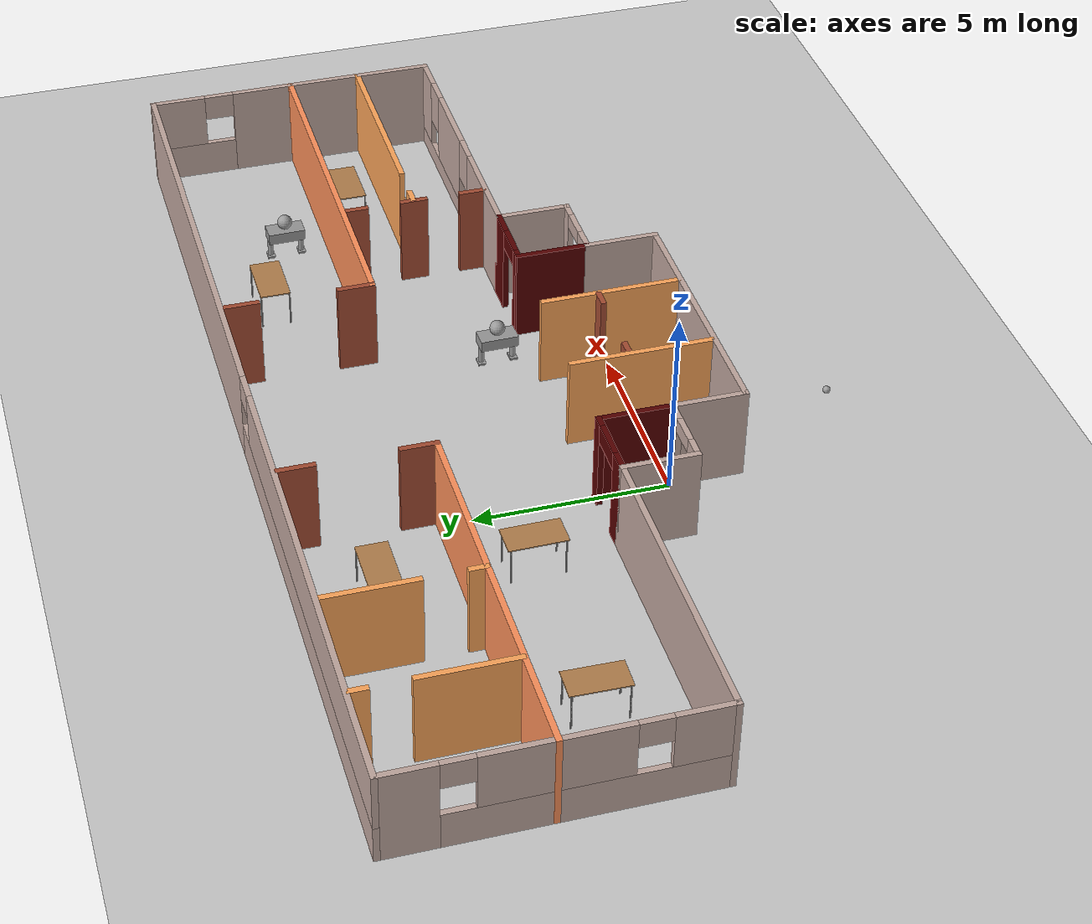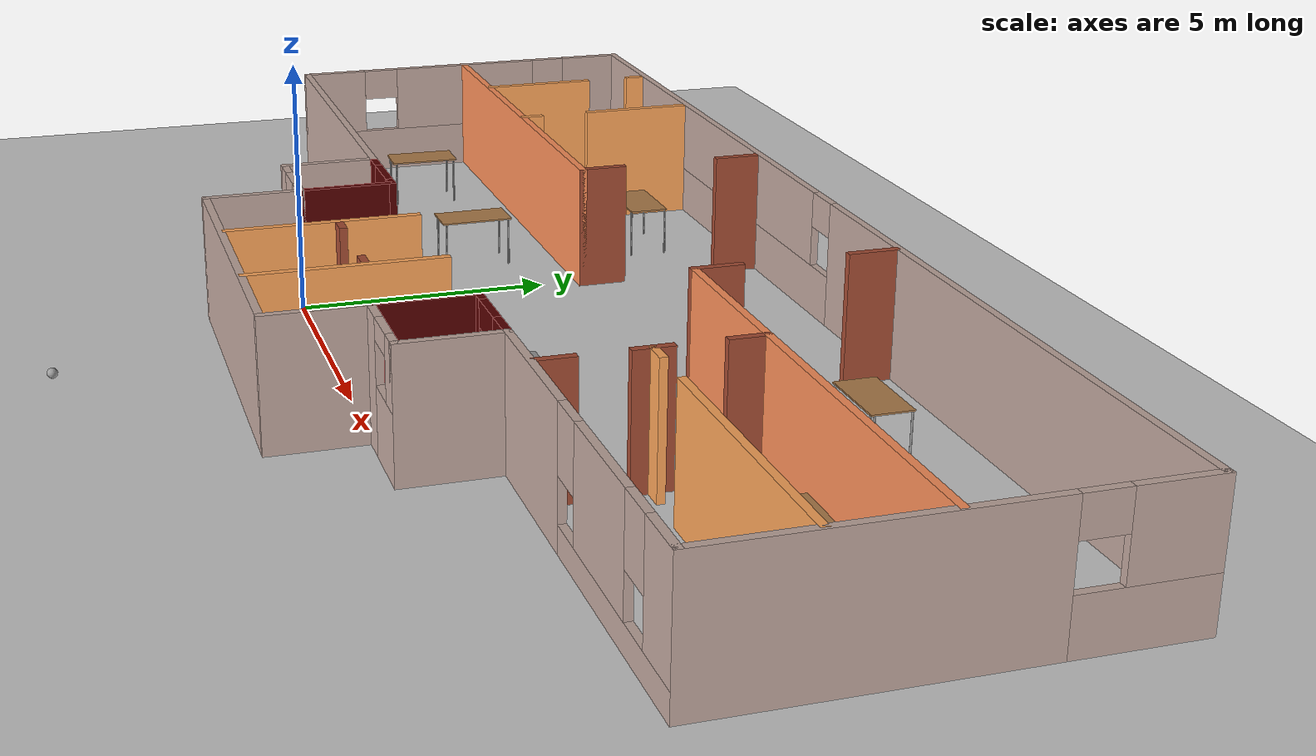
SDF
<sdf version="1.6">
 <world name="default">
  <light name="sun" type="directional">
   <pose>0 0 10 0 -0 0</pose>
   <diffuse>0.8 0.8 0.8 1</diffuse>
   <specular>0.2 0.2 0.2 1</specular>
   <attenuation>
    <range>1000</range>
    <constant>0.9</constant>
    <linear>0.01</linear>
    <quadratic>0.001</quadratic>
   </attenuation>
   <direction>-0.5 0.1 -0.9</direction>
  </light>
  <model name="ground_plane">
   <static>1</static>
   <link name="link">
    <collision name="collision">
     <geometry><plane><normal>0 0 1</normal><size>100 100</size></plane></geometry>
     <surface>
      <contact><collide_bitmask>65535</collide_bitmask></contact>
      <friction><ode><mu>100</mu><mu2>50</mu2></ode></friction>
     </surface>
    </collision>
    <visual name="visual">
     <cast_shadows>0</cast_shadows>
     <geometry><plane><normal>0 0 1</normal><size>100 100</size></plane></geometry>
     <material>
      <script><uri>file://media/materials/scripts/gazebo.material</uri><name>Gazebo/Grey</name></script>
     </material>
    </visual>
   </link>
  </model>
  <gravity>0 0 -9.8</gravity>
  <magnetic_field>6e-06 2.3e-05 -4.2e-05</magnetic_field>
  <atmosphere type="adiabatic"/>
  <physics name="default_physics" default="0" type="ode">
   <max_step_size>0.001</max_step_size>
   <real_time_factor>1</real_time_factor>
   <real_time_update_rate>1000</real_time_update_rate>
  </physics>
  <scene><ambient>0.4 0.4 0.4 1</ambient><background>0.7 0.7 0.7 1</background><shadows>1</shadows></scene>
  <spherical_coordinates>
   <surface_model>EARTH_WGS84</surface_model>
   <latitude_deg>0</latitude_deg>
   <longitude_deg>0</longitude_deg>
   <elevation>0</elevation>
   <heading_deg>0</heading_deg>
  </spherical_coordinates>
  <model name="model">
   <pose>3.47044 3.95113 0 0 -0 0</pose>
   <link name="Wall_10">
    <pose>4.35076 -3.925 0 0 -0 0</pose>
    <visual name="Wall_10_Visual_0">
     <pose>-0.647646 0 1.25 0 -0 0</pose>
     <geometry><box><size>0.704708 0.15 2.5</size></box></geometry>
     <material>
      <script><uri>file://media/materials/scripts/gazebo.material</uri><name>Gazebo/Grey</name></script>
      <ambient>0.760784 0.662745 0.627451 1</ambient>
     </material>
     <meta><layer>0</layer></meta>
    </visual>
    <collision name="Wall_10_Collision_0">
     <geometry><box><size>0.704708 0.15 2.5</size></box></geometry>
     <pose>-0.647646 0 1.25 0 -0 0</pose>
    </collision>
    <visual name="Wall_10_Visual_1">
     <pose>0.352354 0 0.65 0 -0 0</pose>
     <geometry><box><size>1.29529 0.15 1.3</size></box></geometry>
     <material>
      <script><uri>file://media/materials/scripts/gazebo.material</uri><name>Gazebo/Grey</name></script>
      <ambient>0.760784 0.662745 0.627451 1</ambient>
     </material>
     <meta><layer>0</layer></meta>
    </visual>
    <collision name="Wall_10_Collision_1">
     <geometry><box><size>1.29529 0.15 1.3</size></box></geometry>
     <pose>0.352354 0 0.65 0 -0 0</pose>
    </collision>
    <visual name="Wall_10_Visual_2">
     <pose>0.752354 0 1.9 0 -0 0</pose>
     <geometry><box><size>0.495292 0.15 1.2</size></box></geometry>
     <material>
      <script><uri>file://media/materials/scripts/gazebo.material</uri><name>Gazebo/Grey</name></script>
      <ambient>0.760784 0.662745 0.627451 1</ambient>
     </material>
     <meta><layer>0</layer></meta>
    </visual>
    <collision name="Wall_10_Collision_2">
     <geometry><box><size>0.495292 0.15 1.2</size></box></geometry>
     <pose>0.752354 0 1.9 0 -0 0</pose>
    </collision>
    <visual name="Wall_10_Visual_3">
     <pose>0.104708 0 2.3 0 -0 0</pose>
     <geometry><box><size>0.8 0.15 0.4</size></box></geometry>
     <material>
      <script><uri>file://media/materials/scripts/gazebo.material</uri><name>Gazebo/Grey</name></script>
      <ambient>0.760784 0.662745 0.627451 1</ambient>
     </material>
     <meta><layer>0</layer></meta>
    </visual>
    <collision name="Wall_10_Collision_3">
     <geometry><box><size>0.8 0.15 0.4</size></box></geometry>
     <pose>0.104708 0 2.3 0 -0 0</pose>
    </collision>
   </link>
   <link name="Wall_11">
    <collision name="Wall_11_Collision">
     <geometry><box><size>2 0.15 2.5</size></box></geometry>
     <pose>0 0 1.25 0 -0 0</pose>
    </collision>
    <visual name="Wall_11_Visual">
     <pose>0 0 1.25 0 -0 0</pose>
     <geometry><box><size>2 0.15 2.5</size></box></geometry>
     <material>
      <script><uri>file://media/materials/scripts/gazebo.material</uri><name>Gazebo/Grey</name></script>
      <ambient>0.760784 0.662745 0.627451 1</ambient>
     </material>
     <meta><layer>0</layer></meta>
    </visual>
    <pose>5.27576 -3 0 0 -0 1.5708</pose>
   </link>
   <link name="Wall_12">
    <pose>9.20076 -2.075 0 0 -0 0</pose>
    <visual name="Wall_12_Visual_0">
     <pose>-2.47082 0 1.25 0 -0 0</pose>
     <geometry><box><size>3.05836 0.15 2.5</size></box></geometry>
     <material>
      <script><uri>file://media/materials/scripts/gazebo.material</uri><name>Gazebo/Grey</name></script>
      <ambient>0.760784 0.662745 0.627451 1</ambient>
     </material>
     <meta><layer>0</layer></meta>
    </visual>
    <collision name="Wall_12_Collision_0">
     <geometry><box><size>3.05836 0.15 2.5</size></box></geometry>
     <pose>-2.47082 0 1.25 0 -0 0</pose>
    </collision>
    <visual name="Wall_12_Visual_1">
     <pose>1.52918 0 0.25 0 -0 0</pose>
     <geometry><box><size>4.94164 0.15 0.5</size></box></geometry>
     <material>
      <script><uri>file://media/materials/scripts/gazebo.material</uri><name>Gazebo/Grey</name></script>
      <ambient>0.760784 0.662745 0.627451 1</ambient>
     </material>
     <meta><layer>0</layer></meta>
    </visual>
    <collision name="Wall_12_Collision_1">
     <geometry><box><size>4.94164 0.15 0.5</size></box></geometry>
     <pose>1.52918 0 0.25 0 -0 0</pose>
    </collision>
    <visual name="Wall_12_Visual_2">
     <pose>0.995093 0 1.5 0 -0 0</pose>
     <geometry><box><size>2.27347 0.15 2</size></box></geometry>
     <material>
      <script><uri>file://media/materials/scripts/gazebo.material</uri><name>Gazebo/Grey</name></script>
      <ambient>0.760784 0.662745 0.627451 1</ambient>
     </material>
     <meta><layer>0</layer></meta>
    </visual>
    <collision name="Wall_12_Collision_2">
     <geometry><box><size>2.27347 0.15 2</size></box></geometry>
     <pose>0.995093 0 1.5 0 -0 0</pose>
    </collision>
    <visual name="Wall_12_Visual_3">
     <pose>3.46591 0 1.5 0 -0 0</pose>
     <geometry><box><size>1.06817 0.15 2</size></box></geometry>
     <material>
      <script><uri>file://media/materials/scripts/gazebo.material</uri><name>Gazebo/Grey</name></script>
      <ambient>0.760784 0.662745 0.627451 1</ambient>
     </material>
     <meta><layer>0</layer></meta>
    </visual>
    <collision name="Wall_12_Collision_3">
     <geometry><box><size>1.06817 0.15 2</size></box></geometry>
     <pose>3.46591 0 1.5 0 -0 0</pose>
    </collision>
    <visual name="Wall_12_Visual_4">
     <pose>-0.54164 0 1.9 0 -0 0</pose>
     <geometry><box><size>0.8 0.15 1.2</size></box></geometry>
     <material>
      <script><uri>file://media/materials/scripts/gazebo.material</uri><name>Gazebo/Grey</name></script>
      <ambient>0.760784 0.662745 0.627451 1</ambient>
     </material>
     <meta><layer>0</layer></meta>
    </visual>
    <collision name="Wall_12_Collision_4">
     <geometry><box><size>0.8 0.15 1.2</size></box></geometry>
     <pose>-0.54164 0 1.9 0 -0 0</pose>
    </collision>
    <visual name="Wall_12_Visual_5">
     <pose>2.53183 0 1.9 0 -0 0</pose>
     <geometry><box><size>0.8 0.15 1.2</size></box></geometry>
     <material>
      <script><uri>file://media/materials/scripts/gazebo.material</uri><name>Gazebo/Grey</name></script>
      <ambient>0.760784 0.662745 0.627451 1</ambient>
     </material>
     <meta><layer>0</layer></meta>
    </visual>
    <collision name="Wall_12_Collision_5">
     <geometry><box><size>0.8 0.15 1.2</size></box></geometry>
     <pose>2.53183 0 1.9 0 -0 0</pose>
    </collision>
   </link>
   <link name="Wall_13">
    <pose>13.1258 1.85 0 0 -0 1.5708</pose>
    <visual name="Wall_13_Visual_0">
     <pose>-1.15834 0 1.25 0 -0 0</pose>
     <geometry><box><size>5.68331 0.15 2.5</size></box></geometry>
     <material>
      <script><uri>file://media/materials/scripts/gazebo.material</uri><name>Gazebo/Grey</name></script>
      <ambient>0.760784 0.662745 0.627451 1</ambient>
     </material>
     <meta><layer>0</layer></meta>
    </visual>
    <collision name="Wall_13_Collision_0">
     <geometry><box><size>5.68331 0.15 2.5</size></box></geometry>
     <pose>-1.15834 0 1.25 0 -0 0</pose>
    </collision>
    <visual name="Wall_13_Visual_1">
     <pose>2.84165 0 0.5 0 -0 0</pose>
     <geometry><box><size>2.31669 0.15 1</size></box></geometry>
     <material>
      <script><uri>file://media/materials/scripts/gazebo.material</uri><name>Gazebo/Grey</name></script>
      <ambient>0.760784 0.662745 0.627451 1</ambient>
     </material>
     <meta><layer>0</layer></meta>
    </visual>
    <collision name="Wall_13_Collision_1">
     <geometry><box><size>2.31669 0.15 1</size></box></geometry>
     <pose>2.84165 0 0.5 0 -0 0</pose>
    </collision>
    <visual name="Wall_13_Visual_2">
     <pose>3.24166 0 1.75 0 -0 0</pose>
     <geometry><box><size>1.51669 0.15 1.5</size></box></geometry>
     <material>
      <script><uri>file://media/materials/scripts/gazebo.material</uri><name>Gazebo/Grey</name></script>
      <ambient>0.760784 0.662745 0.627451 1</ambient>
     </material>
     <meta><layer>0</layer></meta>
    </visual>
    <collision name="Wall_13_Collision_2">
     <geometry><box><size>1.51669 0.15 1.5</size></box></geometry>
     <pose>3.24166 0 1.75 0 -0 0</pose>
    </collision>
    <visual name="Wall_13_Visual_3">
     <pose>2.08331 0 2.15 0 -0 0</pose>
     <geometry><box><size>0.8 0.15 0.7</size></box></geometry>
     <material>
      <script><uri>file://media/materials/scripts/gazebo.material</uri><name>Gazebo/Grey</name></script>
      <ambient>0.760784 0.662745 0.627451 1</ambient>
     </material>
     <meta><layer>0</layer></meta>
    </visual>
    <collision name="Wall_13_Collision_3">
     <geometry><box><size>0.8 0.15 0.7</size></box></geometry>
     <pose>2.08331 0 2.15 0 -0 0</pose>
    </collision>
   </link>
   <link name="Wall_14">
    <pose>0.000761 5.775 0 0 -0 3.14159</pose>
    <visual name="Wall_14_Visual_0">
     <pose>-6.79874 0 1.25 0 -0 0</pose>
     <geometry><box><size>12.8025 0.15 2.5</size></box></geometry>
     <material>
      <script><uri>file://media/materials/scripts/gazebo.material</uri><name>Gazebo/Grey</name></script>
      <ambient>0.760784 0.662745 0.627451 1</ambient>
     </material>
     <meta><layer>0</layer></meta>
    </visual>
    <collision name="Wall_14_Collision_0">
     <geometry><box><size>12.8025 0.15 2.5</size></box></geometry>
     <pose>-6.79874 0 1.25 0 -0 0</pose>
    </collision>
    <visual name="Wall_14_Visual_1">
     <pose>6.40126 0 0.5 0 -0 0</pose>
     <geometry><box><size>13.5975 0.15 1</size></box></geometry>
     <material>
      <script><uri>file://media/materials/scripts/gazebo.material</uri><name>Gazebo/Grey</name></script>
      <ambient>0.760784 0.662745 0.627451 1</ambient>
     </material>
     <meta><layer>0</layer></meta>
    </visual>
    <collision name="Wall_14_Collision_1">
     <geometry><box><size>13.5975 0.15 1</size></box></geometry>
     <pose>6.40126 0 0.5 0 -0 0</pose>
    </collision>
    <visual name="Wall_14_Visual_2">
     <pose>6.80126 0 1.75 0 -0 0</pose>
     <geometry><box><size>12.7975 0.15 1.5</size></box></geometry>
     <material>
      <script><uri>file://media/materials/scripts/gazebo.material</uri><name>Gazebo/Grey</name></script>
      <ambient>0.760784 0.662745 0.627451 1</ambient>
     </material>
     <meta><layer>0</layer></meta>
    </visual>
    <collision name="Wall_14_Collision_2">
     <geometry><box><size>12.7975 0.15 1.5</size></box></geometry>
     <pose>6.80126 0 1.75 0 -0 0</pose>
    </collision>
    <visual name="Wall_14_Visual_3">
     <pose>0.002526 0 2.15 0 -0 0</pose>
     <geometry><box><size>0.8 0.15 0.7</size></box></geometry>
     <material>
      <script><uri>file://media/materials/scripts/gazebo.material</uri><name>Gazebo/Grey</name></script>
      <ambient>0.760784 0.662745 0.627451 1</ambient>
     </material>
     <meta><layer>0</layer></meta>
    </visual>
    <collision name="Wall_14_Collision_3">
     <geometry><box><size>0.8 0.15 0.7</size></box></geometry>
     <pose>0.002526 0 2.15 0 -0 0</pose>
    </collision>
   </link>
   <link name="Wall_17">
    <collision name="Wall_17_Collision">
     <geometry><box><size>2 0.15 2.5</size></box></geometry>
     <pose>0 0 1.25 0 -0 0</pose>
    </collision>
    <visual name="Wall_17_Visual">
     <pose>0 0 1.25 0 -0 0</pose>
     <geometry><box><size>2 0.15 2.5</size></box></geometry>
     <material>
      <script><uri>file://media/materials/scripts/gazebo.material</uri><name>Gazebo/Grey</name></script>
      <ambient>0.333333 0 0 1</ambient>
     </material>
     <meta><layer>0</layer></meta>
    </visual>
    <pose>-3.42424 -3 0 0 -0 1.5708</pose>
   </link>
   <link name="Wall_19">
    <collision name="Wall_19_Collision">
     <geometry><box><size>2 0.15 2.5</size></box></geometry>
     <pose>0 0 1.25 0 -0 0</pose>
    </collision>
    <visual name="Wall_19_Visual">
     <pose>0 0 1.25 0 -0 0</pose>
     <geometry><box><size>2 0.15 2.5</size></box></geometry>
     <material>
      <script><uri>file://media/materials/scripts/gazebo.material</uri><name>Gazebo/Grey</name></script>
      <ambient>0.333333 0 0 1</ambient>
     </material>
     <meta><layer>0</layer></meta>
    </visual>
    <pose>3.42576 -3 0 0 -0 1.5708</pose>
   </link>
   <link name="Wall_23">
    <pose>-4.34924 -2.075 0 0 -0 0</pose>
    <visual name="Wall_23_Visual_0">
     <pose>-0.695709 0 1.25 0 -0 0</pose>
     <geometry><box><size>0.608582 0.15 2.5</size></box></geometry>
     <material>
      <script><uri>file://media/materials/scripts/gazebo.material</uri><name>Gazebo/Grey</name></script>
      <ambient>0.333333 0 0 1</ambient>
     </material>
     <meta><layer>0</layer></meta>
    </visual>
    <collision name="Wall_23_Collision_0">
     <geometry><box><size>0.608582 0.15 2.5</size></box></geometry>
     <pose>-0.695709 0 1.25 0 -0 0</pose>
    </collision>
    <visual name="Wall_23_Visual_1">
     <pose>0.821594 0 1.25 0 -0 0</pose>
     <geometry><box><size>0.356813 0.15 2.5</size></box></geometry>
     <material>
      <script><uri>file://media/materials/scripts/gazebo.material</uri><name>Gazebo/Grey</name></script>
      <ambient>0.333333 0 0 1</ambient>
     </material>
     <meta><layer>0</layer></meta>
    </visual>
    <collision name="Wall_23_Collision_1">
     <geometry><box><size>0.356813 0.15 2.5</size></box></geometry>
     <pose>0.821594 0 1.25 0 -0 0</pose>
    </collision>
    <visual name="Wall_23_Visual_2">
     <pose>0.125884 0 2.25 0 -0 0</pose>
     <geometry><box><size>1.03461 0.15 0.5</size></box></geometry>
     <material>
      <script><uri>file://media/materials/scripts/gazebo.material</uri><name>Gazebo/Grey</name></script>
      <ambient>0.333333 0 0 1</ambient>
     </material>
     <meta><layer>0</layer></meta>
    </visual>
    <collision name="Wall_23_Collision_2">
     <geometry><box><size>1.03461 0.15 0.5</size></box></geometry>
     <pose>0.125884 0 2.25 0 -0 0</pose>
    </collision>
   </link>
   <link name="Wall_25">
    <pose>4.35076 -2.075 0 0 -0 0</pose>
    <visual name="Wall_25_Visual_0">
     <pose>-0.82203 0 1.25 0 -0 0</pose>
     <geometry><box><size>0.35594 0.15 2.5</size></box></geometry>
     <material>
      <script><uri>file://media/materials/scripts/gazebo.material</uri><name>Gazebo/Grey</name></script>
      <ambient>0.337255 0 0 1</ambient>
     </material>
     <meta><layer>0</layer></meta>
    </visual>
    <collision name="Wall_25_Collision_0">
     <geometry><box><size>0.35594 0.15 2.5</size></box></geometry>
     <pose>-0.82203 0 1.25 0 -0 0</pose>
    </collision>
    <visual name="Wall_25_Visual_1">
     <pose>0.62797 0 1.25 0 -0 0</pose>
     <geometry><box><size>0.74406 0.15 2.5</size></box></geometry>
     <material>
      <script><uri>file://media/materials/scripts/gazebo.material</uri><name>Gazebo/Grey</name></script>
      <ambient>0.337255 0 0 1</ambient>
     </material>
     <meta><layer>0</layer></meta>
    </visual>
    <collision name="Wall_25_Collision_1">
     <geometry><box><size>0.74406 0.15 2.5</size></box></geometry>
     <pose>0.62797 0 1.25 0 -0 0</pose>
    </collision>
    <visual name="Wall_25_Visual_2">
     <pose>-0.19406 0 2.25 0 -0 0</pose>
     <geometry><box><size>0.9 0.15 0.5</size></box></geometry>
     <material>
      <script><uri>file://media/materials/scripts/gazebo.material</uri><name>Gazebo/Grey</name></script>
      <ambient>0.337255 0 0 1</ambient>
     </material>
     <meta><layer>0</layer></meta>
    </visual>
    <collision name="Wall_25_Collision_2">
     <geometry><box><size>0.9 0.15 0.5</size></box></geometry>
     <pose>-0.19406 0 2.25 0 -0 0</pose>
    </collision>
   </link>
   <link name="Wall_27">
    <collision name="Wall_27_Collision">
     <geometry><box><size>10 0.15 2.5</size></box></geometry>
     <pose>0 0 1.25 0 -0 0</pose>
    </collision>
    <visual name="Wall_27_Visual">
     <pose>0 0 1.25 0 -0 0</pose>
     <geometry><box><size>10 0.15 2.5</size></box></geometry>
     <material>
      <script><uri>file://media/materials/scripts/gazebo.material</uri><name>Gazebo/Grey</name></script>
      <ambient>1 0.568627 0.352941 1</ambient>
     </material>
     <meta><layer>0</layer></meta>
    </visual>
    <pose>-8.20076 1.8559 0 0 -0 0</pose>
   </link>
   <link name="Wall_29">
    <collision name="Wall_29_Collision">
     <geometry><box><size>1 0.15 2.5</size></box></geometry>
     <pose>0 0 1.25 0 -0 0</pose>
    </collision>
    <visual name="Wall_29_Visual">
     <pose>0 0 1.25 0 -0 0</pose>
     <geometry><box><size>1 0.15 2.5</size></box></geometry>
     <material>
      <script><uri>file://media/materials/scripts/gazebo.material</uri><name>Gazebo/Bricks</name></script>
      <ambient>1 1 1 1</ambient>
     </material>
     <meta><layer>0</layer></meta>
    </visual>
    <pose>-3.27576 2.2809 0 0 -0 1.5708</pose>
   </link>
   <link name="Wall_3">
    <pose>-13.1242 1.85 0 0 0 -1.5708</pose>
    <visual name="Wall_3_Visual_0">
     <pose>-3.27577 0 1.25 0 -0 0</pose>
     <geometry><box><size>1.44847 0.15 2.5</size></box></geometry>
     <material>
      <script><uri>file://media/materials/scripts/gazebo.material</uri><name>Gazebo/Grey</name></script>
      <ambient>0.760784 0.662745 0.627451 1</ambient>
     </material>
     <meta><layer>0</layer></meta>
    </visual>
    <collision name="Wall_3_Collision_0">
     <geometry><box><size>1.44847 0.15 2.5</size></box></geometry>
     <pose>-3.27577 0 1.25 0 -0 0</pose>
    </collision>
    <visual name="Wall_3_Visual_1">
     <pose>0.724233 0 0.5 0 -0 0</pose>
     <geometry><box><size>6.55153 0.15 1</size></box></geometry>
     <material>
      <script><uri>file://media/materials/scripts/gazebo.material</uri><name>Gazebo/Grey</name></script>
      <ambient>0.760784 0.662745 0.627451 1</ambient>
     </material>
     <meta><layer>0</layer></meta>
    </visual>
    <collision name="Wall_3_Collision_1">
     <geometry><box><size>6.55153 0.15 1</size></box></geometry>
     <pose>0.724233 0 0.5 0 -0 0</pose>
    </collision>
    <visual name="Wall_3_Visual_2">
     <pose>-0.01388 0 1.75 0 -0 0</pose>
     <geometry><box><size>3.47531 0.15 1.5</size></box></geometry>
     <material>
      <script><uri>file://media/materials/scripts/gazebo.material</uri><name>Gazebo/Grey</name></script>
      <ambient>0.760784 0.662745 0.627451 1</ambient>
     </material>
     <meta><layer>0</layer></meta>
    </visual>
    <collision name="Wall_3_Collision_2">
     <geometry><box><size>3.47531 0.15 1.5</size></box></geometry>
     <pose>-0.01388 0 1.75 0 -0 0</pose>
    </collision>
    <visual name="Wall_3_Visual_3">
     <pose>3.26189 0 1.75 0 -0 0</pose>
     <geometry><box><size>1.47623 0.15 1.5</size></box></geometry>
     <material>
      <script><uri>file://media/materials/scripts/gazebo.material</uri><name>Gazebo/Grey</name></script>
      <ambient>0.760784 0.662745 0.627451 1</ambient>
     </material>
     <meta><layer>0</layer></meta>
    </visual>
    <collision name="Wall_3_Collision_3">
     <geometry><box><size>1.47623 0.15 1.5</size></box></geometry>
     <pose>3.26189 0 1.75 0 -0 0</pose>
    </collision>
    <visual name="Wall_3_Visual_4">
     <pose>-2.15153 0 2.15 0 -0 0</pose>
     <geometry><box><size>0.8 0.15 0.7</size></box></geometry>
     <material>
      <script><uri>file://media/materials/scripts/gazebo.material</uri><name>Gazebo/Grey</name></script>
      <ambient>0.760784 0.662745 0.627451 1</ambient>
     </material>
     <meta><layer>0</layer></meta>
    </visual>
    <collision name="Wall_3_Collision_4">
     <geometry><box><size>0.8 0.15 0.7</size></box></geometry>
     <pose>-2.15153 0 2.15 0 -0 0</pose>
    </collision>
    <visual name="Wall_3_Visual_5">
     <pose>2.12377 0 2.15 0 -0 0</pose>
     <geometry><box><size>0.8 0.15 0.7</size></box></geometry>
     <material>
      <script><uri>file://media/materials/scripts/gazebo.material</uri><name>Gazebo/Grey</name></script>
      <ambient>0.760784 0.662745 0.627451 1</ambient>
     </material>
     <meta><layer>0</layer></meta>
    </visual>
    <collision name="Wall_3_Collision_5">
     <geometry><box><size>0.8 0.15 0.7</size></box></geometry>
     <pose>2.12377 0 2.15 0 -0 0</pose>
    </collision>
   </link>
   <link name="Wall_31">
    <collision name="Wall_31_Collision">
     <geometry><box><size>1 0.15 2.5</size></box></geometry>
     <pose>0 0 1.25 0 -0 0</pose>
    </collision>
    <visual name="Wall_31_Visual">
     <pose>0 0 1.25 0 -0 0</pose>
     <geometry><box><size>1 0.15 2.5</size></box></geometry>
     <material>
      <script><uri>file://media/materials/scripts/gazebo.material</uri><name>Gazebo/Bricks</name></script>
      <ambient>1 1 1 1</ambient>
     </material>
     <meta><layer>0</layer></meta>
    </visual>
    <pose>-3.28723 5.2599 0 0 0 -1.5708</pose>
   </link>
   <link name="Wall_33">
    <collision name="Wall_33_Collision">
     <geometry><box><size>10 0.15 2.5</size></box></geometry>
     <pose>0 0 1.25 0 -0 0</pose>
    </collision>
    <visual name="Wall_33_Visual">
     <pose>0 0 1.25 0 -0 0</pose>
     <geometry><box><size>10 0.15 2.5</size></box></geometry>
     <material>
      <script><uri>file://media/materials/scripts/gazebo.material</uri><name>Gazebo/Grey</name></script>
      <ambient>1 0.568627 0.352941 1</ambient>
     </material>
     <meta><layer>0</layer></meta>
    </visual>
    <pose>8.16802 1.85434 0 0 -0 3.14159</pose>
   </link>
   <link name="Wall_34">
    <collision name="Wall_34_Collision">
     <geometry><box><size>1 0.15 2.5</size></box></geometry>
     <pose>0 0 1.25 0 -0 0</pose>
    </collision>
    <visual name="Wall_34_Visual">
     <pose>0 0 1.25 0 -0 0</pose>
     <geometry><box><size>1 0.15 2.5</size></box></geometry>
     <material>
      <script><uri>file://media/materials/scripts/gazebo.material</uri><name>Gazebo/Bricks</name></script>
      <ambient>1 1 1 1</ambient>
     </material>
     <meta><layer>0</layer></meta>
    </visual>
    <pose>3.23171 2.27934 0 0 -0 1.5708</pose>
   </link>
   <link name="Wall_36">
    <collision name="Wall_36_Collision">
     <geometry><box><size>1 0.15 2.5</size></box></geometry>
     <pose>0 0 1.25 0 -0 0</pose>
    </collision>
    <visual name="Wall_36_Visual">
     <pose>0 0 1.25 0 -0 0</pose>
     <geometry><box><size>1 0.15 2.5</size></box></geometry>
     <material>
      <script><uri>file://media/materials/scripts/gazebo.material</uri><name>Gazebo/Bricks</name></script>
      <ambient>1 1 1 1</ambient>
     </material>
     <meta><layer>0</layer></meta>
    </visual>
    <pose>3.24957 5.26265 0 0 0 -1.5708</pose>
   </link>
   <link name="Wall_4">
    <collision name="Wall_4_Collision">
     <geometry><box><size>8 0.15 2.5</size></box></geometry>
     <pose>0 0 1.25 0 -0 0</pose>
    </collision>
    <visual name="Wall_4_Visual">
     <pose>0 0 1.25 0 -0 0</pose>
     <geometry><box><size>8 0.15 2.5</size></box></geometry>
     <material>
      <script><uri>file://media/materials/scripts/gazebo.material</uri><name>Gazebo/Grey</name></script>
      <ambient>0.760784 0.662745 0.627451 1</ambient>
     </material>
     <meta><layer>0</layer></meta>
    </visual>
    <pose>-9.19924 -2.075 0 0 -0 0</pose>
   </link>
   <link name="Wall_40">
    <collision name="Wall_40_Collision">
     <geometry><box><size>3.75 0.15 2.5</size></box></geometry>
     <pose>0 0 1.25 0 -0 0</pose>
    </collision>
    <visual name="Wall_40_Visual">
     <pose>0 0 1.25 0 -0 0</pose>
     <geometry><box><size>3.75 0.15 2.5</size></box></geometry>
     <material>
      <script><uri>file://media/materials/scripts/gazebo.material</uri><name>Gazebo/Grey</name></script>
      <ambient>1 0.654902 0.352941 1</ambient>
     </material>
     <meta><layer>0</layer></meta>
    </visual>
    <pose>-1.2227 -3.87802 0 0 -0 1.5708</pose>
   </link>
   <link name="Wall_42">
    <collision name="Wall_42_Collision">
     <geometry><box><size>3.75 0.15 2.5</size></box></geometry>
     <pose>0 0 1.25 0 -0 0</pose>
    </collision>
    <visual name="Wall_42_Visual">
     <pose>0 0 1.25 0 -0 0</pose>
     <geometry><box><size>3.75 0.15 2.5</size></box></geometry>
     <material>
      <script><uri>file://media/materials/scripts/gazebo.material</uri><name>Gazebo/Grey</name></script>
      <ambient>1 0.654902 0.352941 1</ambient>
     </material>
     <meta><layer>0</layer></meta>
    </visual>
    <pose>1.36977 -3.93472 0 0 -0 1.5708</pose>
   </link>
   <link name="Wall_44">
    <collision name="Wall_44_Collision">
     <geometry><box><size>0.5 0.15 2.5</size></box></geometry>
     <pose>0 0 1.25 0 -0 0</pose>
    </collision>
    <visual name="Wall_44_Visual">
     <pose>0 0 1.25 0 -0 0</pose>
     <geometry><box><size>0.5 0.15 2.5</size></box></geometry>
     <material>
      <script><uri>file://media/materials/scripts/gazebo.material</uri><name>Gazebo/Bricks</name></script>
      <ambient>1 1 1 1</ambient>
     </material>
     <meta><layer>0</layer></meta>
    </visual>
    <pose>-1.00222 -3.57433 0 0 -0 0</pose>
   </link>
   <link name="Wall_46">
    <collision name="Wall_46_Collision">
     <geometry><box><size>0.5 0.15 2.5</size></box></geometry>
     <pose>0 0 1.25 0 -0 0</pose>
    </collision>
    <visual name="Wall_46_Visual">
     <pose>0 0 1.25 0 -0 0</pose>
     <geometry><box><size>0.5 0.15 2.5</size></box></geometry>
     <material>
      <script><uri>file://media/materials/scripts/gazebo.material</uri><name>Gazebo/Bricks</name></script>
      <ambient>1 1 1 1</ambient>
     </material>
     <meta><layer>0</layer></meta>
    </visual>
    <pose>1.13792 -3.57433 0 0 -0 3.14159</pose>
   </link>
   <link name="Wall_48">
    <collision name="Wall_48_Collision">
     <geometry><box><size>0.5 0.15 2.5</size></box></geometry>
     <pose>0 0 1.25 0 -0 0</pose>
    </collision>
    <visual name="Wall_48_Visual">
     <pose>0 0 1.25 0 -0 0</pose>
     <geometry><box><size>0.5 0.15 2.5</size></box></geometry>
     <material>
      <script><uri>file://media/materials/scripts/gazebo.material</uri><name>Gazebo/Grey</name></script>
      <ambient>1 0.654902 0.352941 1</ambient>
     </material>
     <meta><layer>0</layer></meta>
    </visual>
    <pose>-10.6509 5.51316 0 0 0 -1.5708</pose>
   </link>
   <link name="Wall_5">
    <collision name="Wall_5_Collision">
     <geometry><box><size>2 0.15 2.5</size></box></geometry>
     <pose>0 0 1.25 0 -0 0</pose>
    </collision>
    <visual name="Wall_5_Visual">
     <pose>0 0 1.25 0 -0 0</pose>
     <geometry><box><size>2 0.15 2.5</size></box></geometry>
     <material>
      <script><uri>file://media/materials/scripts/gazebo.material</uri><name>Gazebo/Grey</name></script>
      <ambient>0.760784 0.662745 0.627451 1</ambient>
     </material>
     <meta><layer>0</layer></meta>
    </visual>
    <pose>-5.27424 -3 0 0 0 -1.5708</pose>
   </link>
   <link name="Wall_50">
    <collision name="Wall_50_Collision">
     <geometry><box><size>2.5 0.15 2.5</size></box></geometry>
     <pose>0 0 1.25 0 -0 0</pose>
    </collision>
    <visual name="Wall_50_Visual">
     <pose>0 0 1.25 0 -0 0</pose>
     <geometry><box><size>2.5 0.15 2.5</size></box></geometry>
     <material>
      <script><uri>file://media/materials/scripts/gazebo.material</uri><name>Gazebo/Grey</name></script>
      <ambient>1 0.654902 0.352941 1</ambient>
     </material>
     <meta><layer>0</layer></meta>
    </visual>
    <pose>-10.6378 3.0748 0 0 0 -1.5708</pose>
   </link>
   <link name="Wall_52">
    <collision name="Wall_52_Collision">
     <geometry><box><size>0.5 0.15 2.5</size></box></geometry>
     <pose>0 0 1.25 0 -0 0</pose>
    </collision>
    <visual name="Wall_52_Visual">
     <pose>0 0 1.25 0 -0 0</pose>
     <geometry><box><size>0.5 0.15 2.5</size></box></geometry>
     <material>
      <script><uri>file://media/materials/scripts/gazebo.material</uri><name>Gazebo/Grey</name></script>
      <ambient>1 0.654902 0.352941 1</ambient>
     </material>
     <meta><layer>0</layer></meta>
    </visual>
    <pose>-7.69566 2.05803 0 0 -0 1.5708</pose>
   </link>
   <link name="Wall_54">
    <collision name="Wall_54_Collision">
     <geometry><box><size>2.5 0.15 2.5</size></box></geometry>
     <pose>0 0 1.25 0 -0 0</pose>
    </collision>
    <visual name="Wall_54_Visual">
     <pose>0 0 1.25 0 -0 0</pose>
     <geometry><box><size>2.5 0.15 2.5</size></box></geometry>
     <material>
      <script><uri>file://media/materials/scripts/gazebo.material</uri><name>Gazebo/Grey</name></script>
      <ambient>1 0.654902 0.352941 1</ambient>
     </material>
     <meta><layer>0</layer></meta>
    </visual>
    <pose>-7.70873 4.58793 0 0 -0 1.5708</pose>
   </link>
   <link name="Wall_56">
    <collision name="Wall_56_Collision">
     <geometry><box><size>0.75 0.15 2.5</size></box></geometry>
     <pose>0 0 1.25 0 -0 0</pose>
    </collision>
    <visual name="Wall_56_Visual">
     <pose>0 0 1.25 0 -0 0</pose>
     <geometry><box><size>0.75 0.15 2.5</size></box></geometry>
     <material>
      <script><uri>file://media/materials/scripts/gazebo.material</uri><name>Gazebo/Bricks</name></script>
      <ambient>1 1 1 1</ambient>
     </material>
     <meta><layer>0</layer></meta>
    </visual>
    <pose>6.59323 1.52679 0 0 0 -1.5708</pose>
   </link>
   <link name="Wall_58">
    <collision name="Wall_58_Collision">
     <geometry><box><size>0.75 0.15 2.5</size></box></geometry>
     <pose>0 0 1.25 0 -0 0</pose>
    </collision>
    <visual name="Wall_58_Visual">
     <pose>0 0 1.25 0 -0 0</pose>
     <geometry><box><size>0.75 0.15 2.5</size></box></geometry>
     <material>
      <script><uri>file://media/materials/scripts/gazebo.material</uri><name>Gazebo/Bricks</name></script>
      <ambient>1 1 1 1</ambient>
     </material>
     <meta><layer>0</layer></meta>
    </visual>
    <pose>6.59695 -1.70286 0 0 -0 1.5708</pose>
   </link>
   <link name="Wall_6">
    <pose>-4.34924 -3.925 0 0 -0 0</pose>
    <visual name="Wall_6_Visual_0">
     <pose>-0.698028 0 1.25 0 -0 0</pose>
     <geometry><box><size>0.603944 0.15 2.5</size></box></geometry>
     <material>
      <script><uri>file://media/materials/scripts/gazebo.material</uri><name>Gazebo/Grey</name></script>
      <ambient>0.760784 0.662745 0.627451 1</ambient>
     </material>
     <meta><layer>0</layer></meta>
    </visual>
    <collision name="Wall_6_Collision_0">
     <geometry><box><size>0.603944 0.15 2.5</size></box></geometry>
     <pose>-0.698028 0 1.25 0 -0 0</pose>
    </collision>
    <visual name="Wall_6_Visual_1">
     <pose>0.301972 0 0.65 0 -0 0</pose>
     <geometry><box><size>1.39606 0.15 1.3</size></box></geometry>
     <material>
      <script><uri>file://media/materials/scripts/gazebo.material</uri><name>Gazebo/Grey</name></script>
      <ambient>0.760784 0.662745 0.627451 1</ambient>
     </material>
     <meta><layer>0</layer></meta>
    </visual>
    <collision name="Wall_6_Collision_1">
     <geometry><box><size>1.39606 0.15 1.3</size></box></geometry>
     <pose>0.301972 0 0.65 0 -0 0</pose>
    </collision>
    <visual name="Wall_6_Visual_2">
     <pose>0.701972 0 1.9 0 -0 0</pose>
     <geometry><box><size>0.596056 0.15 1.2</size></box></geometry>
     <material>
      <script><uri>file://media/materials/scripts/gazebo.material</uri><name>Gazebo/Grey</name></script>
      <ambient>0.760784 0.662745 0.627451 1</ambient>
     </material>
     <meta><layer>0</layer></meta>
    </visual>
    <collision name="Wall_6_Collision_2">
     <geometry><box><size>0.596056 0.15 1.2</size></box></geometry>
     <pose>0.701972 0 1.9 0 -0 0</pose>
    </collision>
    <visual name="Wall_6_Visual_3">
     <pose>0.003944 0 2.3 0 -0 0</pose>
     <geometry><box><size>0.8 0.15 0.4</size></box></geometry>
     <material>
      <script><uri>file://media/materials/scripts/gazebo.material</uri><name>Gazebo/Grey</name></script>
      <ambient>0.760784 0.662745 0.627451 1</ambient>
     </material>
     <meta><layer>0</layer></meta>
    </visual>
    <collision name="Wall_6_Collision_3">
     <geometry><box><size>0.8 0.15 0.4</size></box></geometry>
     <pose>0.003944 0 2.3 0 -0 0</pose>
    </collision>
   </link>
   <link name="Wall_60">
    <collision name="Wall_60_Collision">
     <geometry><box><size>0.75 0.15 2.5</size></box></geometry>
     <pose>0 0 1.25 0 -0 0</pose>
    </collision>
    <visual name="Wall_60_Visual">
     <pose>0 0 1.25 0 -0 0</pose>
     <geometry><box><size>0.75 0.15 2.5</size></box></geometry>
     <material>
      <script><uri>file://media/materials/scripts/gazebo.material</uri><name>Gazebo/Bricks</name></script>
      <ambient>1 1 1 1</ambient>
     </material>
     <meta><layer>0</layer></meta>
    </visual>
    <pose>6.59837 -0.088973 0 0 0 -1.5708</pose>
   </link>
   <link name="Wall_63">
    <collision name="Wall_63_Collision">
     <geometry><box><size>0.5 0.15 2.5</size></box></geometry>
     <pose>0 0 1.25 0 -0 0</pose>
    </collision>
    <visual name="Wall_63_Visual">
     <pose>0 0 1.25 0 -0 0</pose>
     <geometry><box><size>0.5 0.15 2.5</size></box></geometry>
     <material>
      <script><uri>file://media/materials/scripts/gazebo.material</uri><name>Gazebo/Grey</name></script>
      <ambient>1 0.654902 0.352941 1</ambient>
     </material>
     <meta><layer>0</layer></meta>
    </visual>
    <pose>6.82789 -0.082364 0 0 -0 0</pose>
   </link>
   <link name="Wall_66">
    <collision name="Wall_66_Collision">
     <geometry><box><size>5.25 0.15 2.5</size></box></geometry>
     <pose>0 0 1.25 0 -0 0</pose>
    </collision>
    <visual name="Wall_66_Visual">
     <pose>0 0 1.25 0 -0 0</pose>
     <geometry><box><size>5.25 0.15 2.5</size></box></geometry>
     <material>
      <script><uri>file://media/materials/scripts/gazebo.material</uri><name>Gazebo/Grey</name></script>
      <ambient>1 0.654902 0.352941 1</ambient>
     </material>
     <meta><layer>0</layer></meta>
    </visual>
    <pose>10.5259 -0.093263 0 0 -0 0</pose>
   </link>
   <link name="Wall_7">
    <collision name="Wall_7_Collision">
     <geometry><box><size>2 0.15 2.5</size></box></geometry>
     <pose>0 0 1.25 0 -0 0</pose>
    </collision>
    <visual name="Wall_7_Visual">
     <pose>0 0 1.25 0 -0 0</pose>
     <geometry><box><size>2 0.15 2.5</size></box></geometry>
     <material>
      <script><uri>file://media/materials/scripts/gazebo.material</uri><name>Gazebo/Grey</name></script>
      <ambient>0.760784 0.662745 0.627451 1</ambient>
     </material>
     <meta><layer>0</layer></meta>
    </visual>
    <pose>-3.42424 -4.85 0 0 0 -1.5708</pose>
   </link>
   <link name="Wall_8">
    <collision name="Wall_8_Collision">
     <geometry><box><size>7 0.15 2.5</size></box></geometry>
     <pose>0 0 1.25 0 -0 0</pose>
    </collision>
    <visual name="Wall_8_Visual">
     <pose>0 0 1.25 0 -0 0</pose>
     <geometry><box><size>7 0.15 2.5</size></box></geometry>
     <material>
      <script><uri>file://media/materials/scripts/gazebo.material</uri><name>Gazebo/Grey</name></script>
      <ambient>0.760784 0.662745 0.627451 1</ambient>
     </material>
     <meta><layer>0</layer></meta>
    </visual>
    <pose>0.000761 -5.775 0 0 -0 0</pose>
   </link>
   <link name="Wall_9">
    <collision name="Wall_9_Collision">
     <geometry><box><size>2 0.15 2.5</size></box></geometry>
     <pose>0 0 1.25 0 -0 0</pose>
    </collision>
    <visual name="Wall_9_Visual">
     <pose>0 0 1.25 0 -0 0</pose>
     <geometry><box><size>2 0.15 2.5</size></box></geometry>
     <material>
      <script><uri>file://media/materials/scripts/gazebo.material</uri><name>Gazebo/Grey</name></script>
      <ambient>0.760784 0.662745 0.627451 1</ambient>
     </material>
     <meta><layer>0</layer></meta>
    </visual>
    <pose>3.42576 -4.85 0 0 -0 1.5708</pose>
   </link>
   <static>1</static>
  </model>
  <model name="robot">
   <link name="link_0">
    <pose>-0.425 -0.010043 -0.1 0 -0 0</pose>
    <inertial>
     <mass>1</mass>
     <inertia><ixx>0.145833</ixx><ixy>0</ixy><ixz>0</ixz><iyy>0.145833</iyy><iyz>0</iyz><izz>0.125</izz></inertia>
    </inertial>
    <visual name="visual">
     <geometry><cylinder><radius>0.075</radius><length>0.5</length></cylinder></geometry>
     <material>
      <lighting>1</lighting>
      <script><uri>file://media/materials/scripts/gazebo.material</uri><name>Gazebo/Grey</name></script>
      <shader type="pixel"><normal_map>__default__</normal_map></shader>
      <ambient>0.3 0.3 0.3 1</ambient>
      <diffuse>0.7 0.7 0.7 1</diffuse>
      <specular>0.01 0.01 0.01 1</specular>
      <emissive>1 0.2 0.3 1</emissive>
     </material>
    </visual>
    <collision name="collision">
     <geometry><cylinder><radius>0.075</radius><length>0.5</length></cylinder></geometry>
     <surface>
      <friction>
       <ode><mu>1</mu><mu2>1</mu2><fdir1>0 0 0</fdir1><slip1>0</slip1><slip2>0</slip2></ode>
       <torsional>
        <coefficient>1</coefficient>
        <patch_radius>0</patch_radius>
        <surface_radius>0</surface_radius>
        <use_patch_radius>1</use_patch_radius>
        <ode><slip>0</slip></ode>
       </torsional>
      </friction>
      <bounce><restitution_coefficient>0</restitution_coefficient><threshold>1e+06</threshold></bounce>
      <contact>
       <collide_without_contact>0</collide_without_contact>
       <collide_without_contact_bitmask>1</collide_without_contact_bitmask>
       <collide_bitmask>1</collide_bitmask>
       <ode>
        <soft_cfm>0</soft_cfm>
        <soft_erp>0.2</soft_erp>
        <kp>1e+13</kp>
        <kd>1</kd>
        <max_vel>0.01</max_vel>
        <min_depth>0</min_depth>
       </ode>
       <bullet>
        <split_impulse>1</split_impulse>
        <split_impulse_penetration_threshold>-0.01</split_impulse_penetration_threshold>
        <soft_cfm>0</soft_cfm>
        <soft_erp>0.2</soft_erp>
        <kp>1e+13</kp>
        <kd>1</kd>
       </bullet>
      </contact>
     </surface>
    </collision>
   </link>
   <link name="link_0_clone">
    <pose>0.425 -0.012415 -0.1 0 -0 0</pose>
    <inertial>
     <mass>1</mass>
     <inertia><ixx>0.145833</ixx><ixy>0</ixy><ixz>0</ixz><iyy>0.145833</iyy><iyz>0</iyz><izz>0.125</izz></inertia>
    </inertial>
    <visual name="visual">
     <geometry><cylinder><radius>0.075</radius><length>0.5</length></cylinder></geometry>
     <material>
      <lighting>1</lighting>
      <script><uri>file://media/materials/scripts/gazebo.material</uri><name>Gazebo/Grey</name></script>
      <shader type="pixel"><normal_map>__default__</normal_map></shader>
      <ambient>0.3 0.3 0.3 1</ambient>
      <diffuse>0.7 0.7 0.7 1</diffuse>
      <specular>0.01 0.01 0.01 1</specular>
      <emissive>1 0.2 0.3 1</emissive>
     </material>
    </visual>
    <collision name="collision">
     <geometry><cylinder><radius>0.075</radius><length>0.5</length></cylinder></geometry>
     <surface>
      <friction>
       <ode><mu>1</mu><mu2>1</mu2><fdir1>0 0 0</fdir1><slip1>0</slip1><slip2>0</slip2></ode>
       <torsional>
        <coefficient>1</coefficient>
        <patch_radius>0</patch_radius>
        <surface_radius>0</surface_radius>
        <use_patch_radius>1</use_patch_radius>
        <ode><slip>0</slip></ode>
       </torsional>
      </friction>
      <bounce><restitution_coefficient>0</restitution_coefficient><threshold>1e+06</threshold></bounce>
      <contact>
       <collide_without_contact>0</collide_without_contact>
       <collide_without_contact_bitmask>1</collide_without_contact_bitmask>
       <collide_bitmask>1</collide_bitmask>
       <ode>
        <soft_cfm>0</soft_cfm>
        <soft_erp>0.2</soft_erp>
        <kp>1e+13</kp>
        <kd>1</kd>
        <max_vel>0.01</max_vel>
        <min_depth>0</min_depth>
       </ode>
       <bullet>
        <split_impulse>1</split_impulse>
        <split_impulse_penetration_threshold>-0.01</split_impulse_penetration_threshold>
        <soft_cfm>0</soft_cfm>
        <soft_erp>0.2</soft_erp>
        <kp>1e+13</kp>
        <kd>1</kd>
       </bullet>
      </contact>
     </surface>
    </collision>
   </link>
   <link name="link_1">
    <pose>-0.425 -0.010043 -0.375 0 -0 0</pose>
    <inertial>
     <mass>1</mass>
     <inertia>
      <ixx>0.166667</ixx>
      <ixy>0</ixy>
      <ixz>0</ixz>
      <iyy>0.166667</iyy>
      <iyz>0</iyz>
      <izz>0.166667</izz>
     </inertia>
    </inertial>
    <visual name="visual">
     <geometry><box><size>0.2 0.3 0.05</size></box></geometry>
     <material>
      <lighting>1</lighting>
      <script><uri>file://media/materials/scripts/gazebo.material</uri><name>Gazebo/Grey</name></script>
      <shader type="pixel"><normal_map>__default__</normal_map></shader>
      <ambient>0.3 0.3 0.3 1</ambient>
      <diffuse>0.7 0.7 0.7 1</diffuse>
      <specular>0.01 0.01 0.01 1</specular>
      <emissive>0.2 1 0.2 1</emissive>
     </material>
    </visual>
    <collision name="collision">
     <geometry><box><size>0.2 0.3 0.05</size></box></geometry>
     <surface>
      <friction>
       <ode><mu>1</mu><mu2>1</mu2><fdir1>0 0 0</fdir1><slip1>0</slip1><slip2>0</slip2></ode>
       <torsional>
        <coefficient>1</coefficient>
        <patch_radius>0</patch_radius>
        <surface_radius>0</surface_radius>
        <use_patch_radius>1</use_patch_radius>
        <ode><slip>0</slip></ode>
       </torsional>
      </friction>
      <bounce><restitution_coefficient>0</restitution_coefficient><threshold>1e+06</threshold></bounce>
      <contact>
       <collide_without_contact>0</collide_without_contact>
       <collide_without_contact_bitmask>1</collide_without_contact_bitmask>
       <collide_bitmask>1</collide_bitmask>
       <ode>
        <soft_cfm>0</soft_cfm>
        <soft_erp>0.2</soft_erp>
        <kp>1e+13</kp>
        <kd>1</kd>
        <max_vel>0.01</max_vel>
        <min_depth>0</min_depth>
       </ode>
       <bullet>
        <split_impulse>1</split_impulse>
        <split_impulse_penetration_threshold>-0.01</split_impulse_penetration_threshold>
        <soft_cfm>0</soft_cfm>
        <soft_erp>0.2</soft_erp>
        <kp>1e+13</kp>
        <kd>1</kd>
       </bullet>
      </contact>
     </surface>
    </collision>
   </link>
   <link name="link_1_clone">
    <pose>0.425 -0.012415 -0.375 0 -0 0</pose>
    <inertial>
     <mass>1</mass>
     <inertia>
      <ixx>0.166667</ixx>
      <ixy>0</ixy>
      <ixz>0</ixz>
      <iyy>0.166667</iyy>
      <iyz>0</iyz>
      <izz>0.166667</izz>
     </inertia>
    </inertial>
    <visual name="visual">
     <geometry><box><size>0.2 0.3 0.05</size></box></geometry>
     <material>
      <lighting>1</lighting>
      <script><uri>file://media/materials/scripts/gazebo.material</uri><name>Gazebo/Grey</name></script>
      <shader type="pixel"><normal_map>__default__</normal_map></shader>
      <ambient>0.3 0.3 0.3 1</ambient>
      <diffuse>0.7 0.7 0.7 1</diffuse>
      <specular>0.01 0.01 0.01 1</specular>
      <emissive>0.2 1 0.2 1</emissive>
     </material>
    </visual>
    <collision name="collision">
     <geometry><box><size>0.2 0.3 0.05</size></box></geometry>
     <surface>
      <friction>
       <ode><mu>1</mu><mu2>1</mu2><fdir1>0 0 0</fdir1><slip1>0</slip1><slip2>0</slip2></ode>
       <torsional>
        <coefficient>1</coefficient>
        <patch_radius>0</patch_radius>
        <surface_radius>0</surface_radius>
        <use_patch_radius>1</use_patch_radius>
        <ode><slip>0</slip></ode>
       </torsional>
      </friction>
      <bounce><restitution_coefficient>0</restitution_coefficient><threshold>1e+06</threshold></bounce>
      <contact>
       <collide_without_contact>0</collide_without_contact>
       <collide_without_contact_bitmask>1</collide_without_contact_bitmask>
       <collide_bitmask>1</collide_bitmask>
       <ode>
        <soft_cfm>0</soft_cfm>
        <soft_erp>0.2</soft_erp>
        <kp>1e+13</kp>
        <kd>1</kd>
        <max_vel>0.01</max_vel>
        <min_depth>0</min_depth>
       </ode>
       <bullet>
        <split_impulse>1</split_impulse>
        <split_impulse_penetration_threshold>-0.01</split_impulse_penetration_threshold>
        <soft_cfm>0</soft_cfm>
        <soft_erp>0.2</soft_erp>
        <kp>1e+13</kp>
        <kd>1</kd>
       </bullet>
      </contact>
     </surface>
    </collision>
   </link>
   <link name="link_2">
    <pose>0 0.022457 0.3 0 -0 0</pose>
    <inertial>
     <mass>1</mass>
     <inertia>
      <ixx>0.166667</ixx>
      <ixy>0</ixy>
      <ixz>0</ixz>
      <iyy>0.166667</iyy>
      <iyz>0</iyz>
      <izz>0.166667</izz>
     </inertia>
    </inertial>
    <visual name="visual">
     <geometry><box><size>1 0.5 0.3</size></box></geometry>
     <material>
      <lighting>1</lighting>
      <script><uri>file://media/materials/scripts/gazebo.material</uri><name>Gazebo/Grey</name></script>
      <shader type="pixel"><normal_map>__default__</normal_map></shader>
      <ambient>0.3 0.3 0.3 1</ambient>
      <diffuse>0.7 0.7 0.7 1</diffuse>
      <specular>0.01 0.01 0.01 1</specular>
      <emissive>0.2 1 0.2 1</emissive>
     </material>
    </visual>
    <collision name="collision">
     <geometry><box><size>1 0.5 0.3</size></box></geometry>
     <surface>
      <friction>
       <ode><mu>1</mu><mu2>1</mu2><fdir1>0 0 0</fdir1><slip1>0</slip1><slip2>0</slip2></ode>
       <torsional>
        <coefficient>1</coefficient>
        <patch_radius>0</patch_radius>
        <surface_radius>0</surface_radius>
        <use_patch_radius>1</use_patch_radius>
        <ode><slip>0</slip></ode>
       </torsional>
      </friction>
      <bounce><restitution_coefficient>0</restitution_coefficient><threshold>1e+06</threshold></bounce>
      <contact>
       <collide_without_contact>0</collide_without_contact>
       <collide_without_contact_bitmask>1</collide_without_contact_bitmask>
       <collide_bitmask>1</collide_bitmask>
       <ode>
        <soft_cfm>0</soft_cfm>
        <soft_erp>0.2</soft_erp>
        <kp>1e+13</kp>
        <kd>1</kd>
        <max_vel>0.01</max_vel>
        <min_depth>0</min_depth>
       </ode>
       <bullet>
        <split_impulse>1</split_impulse>
        <split_impulse_penetration_threshold>-0.01</split_impulse_penetration_threshold>
        <soft_cfm>0</soft_cfm>
        <soft_erp>0.2</soft_erp>
        <kp>1e+13</kp>
        <kd>1</kd>
       </bullet>
      </contact>
     </surface>
    </collision>
   </link>
   <link name="link_3">
    <pose>-0 0.022457 0.65 0 -0 0</pose>
    <inertial>
     <mass>1</mass>
     <inertia><ixx>0.1</ixx><ixy>0</ixy><ixz>0</ixz><iyy>0.1</iyy><iyz>0</iyz><izz>0.1</izz></inertia>
    </inertial>
    <visual name="visual">
     <geometry><sphere><radius>0.2</radius></sphere></geometry>
     <material>
      <lighting>1</lighting>
      <script><uri>file://media/materials/scripts/gazebo.material</uri><name>Gazebo/Grey</name></script>
      <shader type="pixel"><normal_map>__default__</normal_map></shader>
      <ambient>0.3 0.3 0.3 1</ambient>
      <diffuse>0.7 0.7 0.7 1</diffuse>
      <specular>0.01 0.01 0.01 1</specular>
      <emissive>1 0.2 0.3 1</emissive>
     </material>
    </visual>
    <collision name="collision">
     <geometry><sphere><radius>0.2</radius></sphere></geometry>
     <surface>
      <friction>
       <ode><mu>1</mu><mu2>1</mu2><fdir1>0 0 0</fdir1><slip1>0</slip1><slip2>0</slip2></ode>
       <torsional>
        <coefficient>1</coefficient>
        <patch_radius>0</patch_radius>
        <surface_radius>0</surface_radius>
        <use_patch_radius>1</use_patch_radius>
        <ode><slip>0</slip></ode>
       </torsional>
      </friction>
      <bounce><restitution_coefficient>0</restitution_coefficient><threshold>1e+06</threshold></bounce>
      <contact>
       <collide_without_contact>0</collide_without_contact>
       <collide_without_contact_bitmask>1</collide_without_contact_bitmask>
       <collide_bitmask>1</collide_bitmask>
       <ode>
        <soft_cfm>0</soft_cfm>
        <soft_erp>0.2</soft_erp>
        <kp>1e+13</kp>
        <kd>1</kd>
        <max_vel>0.01</max_vel>
        <min_depth>0</min_depth>
       </ode>
       <bullet>
        <split_impulse>1</split_impulse>
        <split_impulse_penetration_threshold>-0.01</split_impulse_penetration_threshold>
        <soft_cfm>0</soft_cfm>
        <soft_erp>0.2</soft_erp>
        <kp>1e+13</kp>
        <kd>1</kd>
       </bullet>
      </contact>
     </surface>
    </collision>
   </link>
   <joint name="link_0_JOINT_2" type="fixed">
    <parent>link_0</parent>
    <child>link_2</child>
    <physics>
     <ode><limit><cfm>0</cfm><erp>0.2</erp></limit><suspension><cfm>0</cfm><erp>0.2</erp></suspension></ode>
    </physics>
   </joint>
   <joint name="link_0_clone_JOINT_6" type="revolute">
    <parent>link_0_clone</parent>
    <child>link_1_clone</child>
    <axis>
     <xyz>1 0 0</xyz>
     <use_parent_model_frame>0</use_parent_model_frame>
     <limit>
      <lower>-1.79769e+308</lower>
      <upper>1.79769e+308</upper>
      <effort>-1</effort>
      <velocity>-1</velocity>
     </limit>
     <dynamics>
      <spring_reference>0</spring_reference>
      <spring_stiffness>0</spring_stiffness>
      <damping>0</damping>
      <friction>0</friction>
     </dynamics>
    </axis>
    <physics>
     <ode><limit><cfm>0</cfm><erp>0.2</erp></limit><suspension><cfm>0</cfm><erp>0.2</erp></suspension></ode>
    </physics>
   </joint>
   <joint name="link_1_JOINT_0" type="fixed">
    <parent>link_1</parent>
    <child>link_0</child>
    <pose>0 0 -0.25 0 -0 0</pose>
    <physics>
     <ode><limit><cfm>0</cfm><erp>0.2</erp></limit><suspension><cfm>0</cfm><erp>0.2</erp></suspension></ode>
    </physics>
   </joint>
   <joint name="link_2_JOINT_5" type="fixed">
    <parent>link_2</parent>
    <child>link_0_clone</child>
    <physics>
     <ode><limit><cfm>0</cfm><erp>0.2</erp></limit><suspension><cfm>0</cfm><erp>0.2</erp></suspension></ode>
    </physics>
   </joint>
   <joint name="link_2_JOINT_7" type="fixed">
    <parent>link_2</parent>
    <child>link_3</child>
    <physics>
     <ode><limit><cfm>0</cfm><erp>0.2</erp></limit><suspension><cfm>0</cfm><erp>0.2</erp></suspension></ode>
    </physics>
   </joint>
   <static>0</static>
   <pose>5.94345 2.71776 0.4 -0 -1e-06 1.58896</pose>
  </model>
  <model name="robot_clone">
   <link name="link_0">
    <pose>-0.425 -0.010043 -0.1 0 -0 0</pose>
    <inertial>
     <mass>1</mass>
     <inertia><ixx>0.145833</ixx><ixy>0</ixy><ixz>0</ixz><iyy>0.145833</iyy><iyz>0</iyz><izz>0.125</izz></inertia>
    </inertial>
    <visual name="visual">
     <geometry><cylinder><radius>0.075</radius><length>0.5</length></cylinder></geometry>
     <material>
      <lighting>1</lighting>
      <script><uri>file://media/materials/scripts/gazebo.material</uri><name>Gazebo/Grey</name></script>
      <shader type="pixel"><normal_map>__default__</normal_map></shader>
      <ambient>0.3 0.3 0.3 1</ambient>
      <diffuse>0.7 0.7 0.7 1</diffuse>
      <specular>0.01 0.01 0.01 1</specular>
      <emissive>1 0.2 0.3 1</emissive>
     </material>
    </visual>
    <collision name="collision">
     <geometry><cylinder><radius>0.075</radius><length>0.5</length></cylinder></geometry>
     <surface>
      <friction>
       <ode><mu>1</mu><mu2>1</mu2><fdir1>0 0 0</fdir1><slip1>0</slip1><slip2>0</slip2></ode>
       <torsional>
        <coefficient>1</coefficient>
        <patch_radius>0</patch_radius>
        <surface_radius>0</surface_radius>
        <use_patch_radius>1</use_patch_radius>
        <ode><slip>0</slip></ode>
       </torsional>
      </friction>
      <bounce><restitution_coefficient>0</restitution_coefficient><threshold>1e+06</threshold></bounce>
      <contact>
       <collide_without_contact>0</collide_without_contact>
       <collide_without_contact_bitmask>1</collide_without_contact_bitmask>
       <collide_bitmask>1</collide_bitmask>
       <ode>
        <soft_cfm>0</soft_cfm>
        <soft_erp>0.2</soft_erp>
        <kp>1e+13</kp>
        <kd>1</kd>
        <max_vel>0.01</max_vel>
        <min_depth>0</min_depth>
       </ode>
       <bullet>
        <split_impulse>1</split_impulse>
        <split_impulse_penetration_threshold>-0.01</split_impulse_penetration_threshold>
        <soft_cfm>0</soft_cfm>
        <soft_erp>0.2</soft_erp>
        <kp>1e+13</kp>
        <kd>1</kd>
       </bullet>
      </contact>
     </surface>
    </collision>
   </link>
   <link name="link_0_clone">
    <pose>0.425 -0.012415 -0.1 0 -0 0</pose>
    <inertial>
     <mass>1</mass>
     <inertia><ixx>0.145833</ixx><ixy>0</ixy><ixz>0</ixz><iyy>0.145833</iyy><iyz>0</iyz><izz>0.125</izz></inertia>
    </inertial>
    <visual name="visual">
     <geometry><cylinder><radius>0.075</radius><length>0.5</length></cylinder></geometry>
     <material>
      <lighting>1</lighting>
      <script><uri>file://media/materials/scripts/gazebo.material</uri><name>Gazebo/Grey</name></script>
      <shader type="pixel"><normal_map>__default__</normal_map></shader>
      <ambient>0.3 0.3 0.3 1</ambient>
      <diffuse>0.7 0.7 0.7 1</diffuse>
      <specular>0.01 0.01 0.01 1</specular>
      <emissive>1 0.2 0.3 1</emissive>
     </material>
    </visual>
    <collision name="collision">
     <geometry><cylinder><radius>0.075</radius><length>0.5</length></cylinder></geometry>
     <surface>
      <friction>
       <ode><mu>1</mu><mu2>1</mu2><fdir1>0 0 0</fdir1><slip1>0</slip1><slip2>0</slip2></ode>
       <torsional>
        <coefficient>1</coefficient>
        <patch_radius>0</patch_radius>
        <surface_radius>0</surface_radius>
        <use_patch_radius>1</use_patch_radius>
        <ode><slip>0</slip></ode>
       </torsional>
      </friction>
      <bounce><restitution_coefficient>0</restitution_coefficient><threshold>1e+06</threshold></bounce>
      <contact>
       <collide_without_contact>0</collide_without_contact>
       <collide_without_contact_bitmask>1</collide_without_contact_bitmask>
       <collide_bitmask>1</collide_bitmask>
       <ode>
        <soft_cfm>0</soft_cfm>
        <soft_erp>0.2</soft_erp>
        <kp>1e+13</kp>
        <kd>1</kd>
        <max_vel>0.01</max_vel>
        <min_depth>0</min_depth>
       </ode>
       <bullet>
        <split_impulse>1</split_impulse>
        <split_impulse_penetration_threshold>-0.01</split_impulse_penetration_threshold>
        <soft_cfm>0</soft_cfm>
        <soft_erp>0.2</soft_erp>
        <kp>1e+13</kp>
        <kd>1</kd>
       </bullet>
      </contact>
     </surface>
    </collision>
   </link>
   <link name="link_1">
    <pose>-0.425 -0.010043 -0.375 0 -0 0</pose>
    <inertial>
     <mass>1</mass>
     <inertia>
      <ixx>0.166667</ixx>
      <ixy>0</ixy>
      <ixz>0</ixz>
      <iyy>0.166667</iyy>
      <iyz>0</iyz>
      <izz>0.166667</izz>
     </inertia>
    </inertial>
    <visual name="visual">
     <geometry><box><size>0.2 0.3 0.05</size></box></geometry>
     <material>
      <lighting>1</lighting>
      <script><uri>file://media/materials/scripts/gazebo.material</uri><name>Gazebo/Grey</name></script>
      <shader type="pixel"><normal_map>__default__</normal_map></shader>
      <ambient>0.3 0.3 0.3 1</ambient>
      <diffuse>0.7 0.7 0.7 1</diffuse>
      <specular>0.01 0.01 0.01 1</specular>
      <emissive>0.2 1 0.2 1</emissive>
     </material>
    </visual>
    <collision name="collision">
     <geometry><box><size>0.2 0.3 0.05</size></box></geometry>
     <surface>
      <friction>
       <ode><mu>1</mu><mu2>1</mu2><fdir1>0 0 0</fdir1><slip1>0</slip1><slip2>0</slip2></ode>
       <torsional>
        <coefficient>1</coefficient>
        <patch_radius>0</patch_radius>
        <surface_radius>0</surface_radius>
        <use_patch_radius>1</use_patch_radius>
        <ode><slip>0</slip></ode>
       </torsional>
      </friction>
      <bounce><restitution_coefficient>0</restitution_coefficient><threshold>1e+06</threshold></bounce>
      <contact>
       <collide_without_contact>0</collide_without_contact>
       <collide_without_contact_bitmask>1</collide_without_contact_bitmask>
       <collide_bitmask>1</collide_bitmask>
       <ode>
        <soft_cfm>0</soft_cfm>
        <soft_erp>0.2</soft_erp>
        <kp>1e+13</kp>
        <kd>1</kd>
        <max_vel>0.01</max_vel>
        <min_depth>0</min_depth>
       </ode>
       <bullet>
        <split_impulse>1</split_impulse>
        <split_impulse_penetration_threshold>-0.01</split_impulse_penetration_threshold>
        <soft_cfm>0</soft_cfm>
        <soft_erp>0.2</soft_erp>
        <kp>1e+13</kp>
        <kd>1</kd>
       </bullet>
      </contact>
     </surface>
    </collision>
   </link>
   <link name="link_1_clone">
    <pose>0.425 -0.012415 -0.375 0 -0 0</pose>
    <inertial>
     <mass>1</mass>
     <inertia>
      <ixx>0.166667</ixx>
      <ixy>0</ixy>
      <ixz>0</ixz>
      <iyy>0.166667</iyy>
      <iyz>0</iyz>
      <izz>0.166667</izz>
     </inertia>
    </inertial>
    <visual name="visual">
     <geometry><box><size>0.2 0.3 0.05</size></box></geometry>
     <material>
      <lighting>1</lighting>
      <script><uri>file://media/materials/scripts/gazebo.material</uri><name>Gazebo/Grey</name></script>
      <shader type="pixel"><normal_map>__default__</normal_map></shader>
      <ambient>0.3 0.3 0.3 1</ambient>
      <diffuse>0.7 0.7 0.7 1</diffuse>
      <specular>0.01 0.01 0.01 1</specular>
      <emissive>0.2 1 0.2 1</emissive>
     </material>
    </visual>
    <collision name="collision">
     <geometry><box><size>0.2 0.3 0.05</size></box></geometry>
     <surface>
      <friction>
       <ode><mu>1</mu><mu2>1</mu2><fdir1>0 0 0</fdir1><slip1>0</slip1><slip2>0</slip2></ode>
       <torsional>
        <coefficient>1</coefficient>
        <patch_radius>0</patch_radius>
        <surface_radius>0</surface_radius>
        <use_patch_radius>1</use_patch_radius>
        <ode><slip>0</slip></ode>
       </torsional>
      </friction>
      <bounce><restitution_coefficient>0</restitution_coefficient><threshold>1e+06</threshold></bounce>
      <contact>
       <collide_without_contact>0</collide_without_contact>
       <collide_without_contact_bitmask>1</collide_without_contact_bitmask>
       <collide_bitmask>1</collide_bitmask>
       <ode>
        <soft_cfm>0</soft_cfm>
        <soft_erp>0.2</soft_erp>
        <kp>1e+13</kp>
        <kd>1</kd>
        <max_vel>0.01</max_vel>
        <min_depth>0</min_depth>
       </ode>
       <bullet>
        <split_impulse>1</split_impulse>
        <split_impulse_penetration_threshold>-0.01</split_impulse_penetration_threshold>
        <soft_cfm>0</soft_cfm>
        <soft_erp>0.2</soft_erp>
        <kp>1e+13</kp>
        <kd>1</kd>
       </bullet>
      </contact>
     </surface>
    </collision>
   </link>
   <link name="link_2">
    <pose>0 0.022457 0.3 0 -0 0</pose>
    <inertial>
     <mass>1</mass>
     <inertia>
      <ixx>0.166667</ixx>
      <ixy>0</ixy>
      <ixz>0</ixz>
      <iyy>0.166667</iyy>
      <iyz>0</iyz>
      <izz>0.166667</izz>
     </inertia>
    </inertial>
    <visual name="visual">
     <geometry><box><size>1 0.5 0.3</size></box></geometry>
     <material>
      <lighting>1</lighting>
      <script><uri>file://media/materials/scripts/gazebo.material</uri><name>Gazebo/Grey</name></script>
      <shader type="pixel"><normal_map>__default__</normal_map></shader>
      <ambient>0.3 0.3 0.3 1</ambient>
      <diffuse>0.7 0.7 0.7 1</diffuse>
      <specular>0.01 0.01 0.01 1</specular>
      <emissive>0.2 1 0.2 1</emissive>
     </material>
    </visual>
    <collision name="collision">
     <geometry><box><size>1 0.5 0.3</size></box></geometry>
     <surface>
      <friction>
       <ode><mu>1</mu><mu2>1</mu2><fdir1>0 0 0</fdir1><slip1>0</slip1><slip2>0</slip2></ode>
       <torsional>
        <coefficient>1</coefficient>
        <patch_radius>0</patch_radius>
        <surface_radius>0</surface_radius>
        <use_patch_radius>1</use_patch_radius>
        <ode><slip>0</slip></ode>
       </torsional>
      </friction>
      <bounce><restitution_coefficient>0</restitution_coefficient><threshold>1e+06</threshold></bounce>
      <contact>
       <collide_without_contact>0</collide_without_contact>
       <collide_without_contact_bitmask>1</collide_without_contact_bitmask>
       <collide_bitmask>1</collide_bitmask>
       <ode>
        <soft_cfm>0</soft_cfm>
        <soft_erp>0.2</soft_erp>
        <kp>1e+13</kp>
        <kd>1</kd>
        <max_vel>0.01</max_vel>
        <min_depth>0</min_depth>
       </ode>
       <bullet>
        <split_impulse>1</split_impulse>
        <split_impulse_penetration_threshold>-0.01</split_impulse_penetration_threshold>
        <soft_cfm>0</soft_cfm>
        <soft_erp>0.2</soft_erp>
        <kp>1e+13</kp>
        <kd>1</kd>
       </bullet>
      </contact>
     </surface>
    </collision>
   </link>
   <link name="link_3">
    <pose>-0 0.022457 0.65 0 -0 0</pose>
    <inertial>
     <mass>1</mass>
     <inertia><ixx>0.1</ixx><ixy>0</ixy><ixz>0</ixz><iyy>0.1</iyy><iyz>0</iyz><izz>0.1</izz></inertia>
    </inertial>
    <visual name="visual">
     <geometry><sphere><radius>0.2</radius></sphere></geometry>
     <material>
      <lighting>1</lighting>
      <script><uri>file://media/materials/scripts/gazebo.material</uri><name>Gazebo/Grey</name></script>
      <shader type="pixel"><normal_map>__default__</normal_map></shader>
      <ambient>0.3 0.3 0.3 1</ambient>
      <diffuse>0.7 0.7 0.7 1</diffuse>
      <specular>0.01 0.01 0.01 1</specular>
      <emissive>1 0.2 0.3 1</emissive>
     </material>
    </visual>
    <collision name="collision">
     <geometry><sphere><radius>0.2</radius></sphere></geometry>
     <surface>
      <friction>
       <ode><mu>1</mu><mu2>1</mu2><fdir1>0 0 0</fdir1><slip1>0</slip1><slip2>0</slip2></ode>
       <torsional>
        <coefficient>1</coefficient>
        <patch_radius>0</patch_radius>
        <surface_radius>0</surface_radius>
        <use_patch_radius>1</use_patch_radius>
        <ode><slip>0</slip></ode>
       </torsional>
      </friction>
      <bounce><restitution_coefficient>0</restitution_coefficient><threshold>1e+06</threshold></bounce>
      <contact>
       <collide_without_contact>0</collide_without_contact>
       <collide_without_contact_bitmask>1</collide_without_contact_bitmask>
       <collide_bitmask>1</collide_bitmask>
       <ode>
        <soft_cfm>0</soft_cfm>
        <soft_erp>0.2</soft_erp>
        <kp>1e+13</kp>
        <kd>1</kd>
        <max_vel>0.01</max_vel>
        <min_depth>0</min_depth>
       </ode>
       <bullet>
        <split_impulse>1</split_impulse>
        <split_impulse_penetration_threshold>-0.01</split_impulse_penetration_threshold>
        <soft_cfm>0</soft_cfm>
        <soft_erp>0.2</soft_erp>
        <kp>1e+13</kp>
        <kd>1</kd>
       </bullet>
      </contact>
     </surface>
    </collision>
   </link>
   <joint name="link_0_JOINT_2" type="fixed">
    <parent>link_0</parent>
    <child>link_2</child>
    <physics>
     <ode><limit><cfm>0</cfm><erp>0.2</erp></limit><suspension><cfm>0</cfm><erp>0.2</erp></suspension></ode>
    </physics>
   </joint>
   <joint name="link_0_clone_JOINT_6" type="revolute">
    <parent>link_0_clone</parent>
    <child>link_1_clone</child>
    <axis>
     <xyz>1 0 0</xyz>
     <use_parent_model_frame>0</use_parent_model_frame>
     <limit>
      <lower>-1.79769e+308</lower>
      <upper>1.79769e+308</upper>
      <effort>-1</effort>
      <velocity>-1</velocity>
     </limit>
     <dynamics>
      <spring_reference>0</spring_reference>
      <spring_stiffness>0</spring_stiffness>
      <damping>0</damping>
      <friction>0</friction>
     </dynamics>
    </axis>
    <physics>
     <ode><limit><cfm>0</cfm><erp>0.2</erp></limit><suspension><cfm>0</cfm><erp>0.2</erp></suspension></ode>
    </physics>
   </joint>
   <joint name="link_1_JOINT_0" type="fixed">
    <parent>link_1</parent>
    <child>link_0</child>
    <pose>0 0 -0.25 0 -0 0</pose>
    <physics>
     <ode><limit><cfm>0</cfm><erp>0.2</erp></limit><suspension><cfm>0</cfm><erp>0.2</erp></suspension></ode>
    </physics>
   </joint>
   <joint name="link_2_JOINT_5" type="fixed">
    <parent>link_2</parent>
    <child>link_0_clone</child>
    <physics>
     <ode><limit><cfm>0</cfm><erp>0.2</erp></limit><suspension><cfm>0</cfm><erp>0.2</erp></suspension></ode>
    </physics>
   </joint>
   <joint name="link_2_JOINT_7" type="fixed">
    <parent>link_2</parent>
    <child>link_3</child>
    <physics>
     <ode><limit><cfm>0</cfm><erp>0.2</erp></limit><suspension><cfm>0</cfm><erp>0.2</erp></suspension></ode>
    </physics>
   </joint>
   <static>0</static>
   <pose>12.0656 7.01218 0.4 0 -1e-06 1.58894</pose>
  </model>
  <model name="table">
   <static>1</static>
   <link name="link">
    <collision name="surface">
     <pose>0 0 1 0 -0 0</pose>
     <geometry><box><size>1.5 0.8 0.03</size></box></geometry>
     <surface><friction><ode><mu>0.6</mu><mu2>0.6</mu2></ode></friction></surface>
    </collision>
    <visual name="visual1">
     <pose>0 0 1 0 -0 0</pose>
     <geometry><box><size>1.5 0.8 0.03</size></box></geometry>
     <material>
      <script><uri>file://media/materials/scripts/gazebo.material</uri><name>Gazebo/Wood</name></script>
     </material>
    </visual>
    <collision name="front_left_leg">
     <pose>0.68 0.38 0.5 0 -0 0</pose>
     <geometry><cylinder><radius>0.02</radius><length>1</length></cylinder></geometry>
    </collision>
    <visual name="front_left_leg">
     <pose>0.68 0.38 0.5 0 -0 0</pose>
     <geometry><cylinder><radius>0.02</radius><length>1</length></cylinder></geometry>
     <material>
      <script><uri>file://media/materials/scripts/gazebo.material</uri><name>Gazebo/Grey</name></script>
     </material>
    </visual>
    <collision name="front_right_leg">
     <pose>0.68 -0.38 0.5 0 -0 0</pose>
     <geometry><cylinder><radius>0.02</radius><length>1</length></cylinder></geometry>
    </collision>
    <visual name="front_right_leg">
     <pose>0.68 -0.38 0.5 0 -0 0</pose>
     <geometry><cylinder><radius>0.02</radius><length>1</length></cylinder></geometry>
     <material>
      <script><uri>file://media/materials/scripts/gazebo.material</uri><name>Gazebo/Grey</name></script>
     </material>
    </visual>
    <collision name="back_right_leg">
     <pose>-0.68 -0.38 0.5 0 -0 0</pose>
     <geometry><cylinder><radius>0.02</radius><length>1</length></cylinder></geometry>
    </collision>
    <visual name="back_right_leg">
     <pose>-0.68 -0.38 0.5 0 -0 0</pose>
     <geometry><cylinder><radius>0.02</radius><length>1</length></cylinder></geometry>
     <material>
      <script><uri>file://media/materials/scripts/gazebo.material</uri><name>Gazebo/Grey</name></script>
     </material>
    </visual>
    <collision name="back_left_leg">
     <pose>-0.68 0.38 0.5 0 -0 0</pose>
     <geometry><cylinder><radius>0.02</radius><length>1</length></cylinder></geometry>
    </collision>
    <visual name="back_left_leg">
     <pose>-0.68 0.38 0.5 0 -0 0</pose>
     <geometry><cylinder><radius>0.02</radius><length>1</length></cylinder></geometry>
     <material>
      <script><uri>file://media/materials/scripts/gazebo.material</uri><name>Gazebo/Grey</name></script>
     </material>
    </visual>
   </link>
   <pose>-1.99098 7.78386 0 0 -0 0</pose>
  </model>
  <model name="table_0">
   <static>1</static>
   <link name="link">
    <collision name="surface">
     <pose>0 0 1 0 -0 0</pose>
     <geometry><box><size>1.5 0.8 0.03</size></box></geometry>
     <surface><friction><ode><mu>0.6</mu><mu2>0.6</mu2></ode></friction></surface>
    </collision>
    <visual name="visual1">
     <pose>0 0 1 0 -0 0</pose>
     <geometry><box><size>1.5 0.8 0.03</size></box></geometry>
     <material>
      <script><uri>file://media/materials/scripts/gazebo.material</uri><name>Gazebo/Wood</name></script>
     </material>
    </visual>
    <collision name="front_left_leg">
     <pose>0.68 0.38 0.5 0 -0 0</pose>
     <geometry><cylinder><radius>0.02</radius><length>1</length></cylinder></geometry>
    </collision>
    <visual name="front_left_leg">
     <pose>0.68 0.38 0.5 0 -0 0</pose>
     <geometry><cylinder><radius>0.02</radius><length>1</length></cylinder></geometry>
     <material>
      <script><uri>file://media/materials/scripts/gazebo.material</uri><name>Gazebo/Grey</name></script>
     </material>
    </visual>
    <collision name="front_right_leg">
     <pose>0.68 -0.38 0.5 0 -0 0</pose>
     <geometry><cylinder><radius>0.02</radius><length>1</length></cylinder></geometry>
    </collision>
    <visual name="front_right_leg">
     <pose>0.68 -0.38 0.5 0 -0 0</pose>
     <geometry><cylinder><radius>0.02</radius><length>1</length></cylinder></geometry>
     <material>
      <script><uri>file://media/materials/scripts/gazebo.material</uri><name>Gazebo/Grey</name></script>
     </material>
    </visual>
    <collision name="back_right_leg">
     <pose>-0.68 -0.38 0.5 0 -0 0</pose>
     <geometry><cylinder><radius>0.02</radius><length>1</length></cylinder></geometry>
    </collision>
    <visual name="back_right_leg">
     <pose>-0.68 -0.38 0.5 0 -0 0</pose>
     <geometry><cylinder><radius>0.02</radius><length>1</length></cylinder></geometry>
     <material>
      <script><uri>file://media/materials/scripts/gazebo.material</uri><name>Gazebo/Grey</name></script>
     </material>
    </visual>
    <collision name="back_left_leg">
     <pose>-0.68 0.38 0.5 0 -0 0</pose>
     <geometry><cylinder><radius>0.02</radius><length>1</length></cylinder></geometry>
    </collision>
    <visual name="back_left_leg">
     <pose>-0.68 0.38 0.5 0 -0 0</pose>
     <geometry><cylinder><radius>0.02</radius><length>1</length></cylinder></geometry>
     <material>
      <script><uri>file://media/materials/scripts/gazebo.material</uri><name>Gazebo/Grey</name></script>
     </material>
    </visual>
   </link>
   <pose>13.5119 4.96008 0 0 -0 0</pose>
  </model>
  <model name="table_1">
   <static>1</static>
   <link name="link">
    <collision name="surface">
     <pose>0 0 1 0 -0 0</pose>
     <geometry><box><size>1.5 0.8 0.03</size></box></geometry>
     <surface><friction><ode><mu>0.6</mu><mu2>0.6</mu2></ode></friction></surface>
    </collision>
    <visual name="visual1">
     <pose>0 0 1 0 -0 0</pose>
     <geometry><box><size>1.5 0.8 0.03</size></box></geometry>
     <material>
      <script><uri>file://media/materials/scripts/gazebo.material</uri><name>Gazebo/Wood</name></script>
     </material>
    </visual>
    <collision name="front_left_leg">
     <pose>0.68 0.38 0.5 0 -0 0</pose>
     <geometry><cylinder><radius>0.02</radius><length>1</length></cylinder></geometry>
    </collision>
    <visual name="front_left_leg">
     <pose>0.68 0.38 0.5 0 -0 0</pose>
     <geometry><cylinder><radius>0.02</radius><length>1</length></cylinder></geometry>
     <material>
      <script><uri>file://media/materials/scripts/gazebo.material</uri><name>Gazebo/Grey</name></script>
     </material>
    </visual>
    <collision name="front_right_leg">
     <pose>0.68 -0.38 0.5 0 -0 0</pose>
     <geometry><cylinder><radius>0.02</radius><length>1</length></cylinder></geometry>
    </collision>
    <visual name="front_right_leg">
     <pose>0.68 -0.38 0.5 0 -0 0</pose>
     <geometry><cylinder><radius>0.02</radius><length>1</length></cylinder></geometry>
     <material>
      <script><uri>file://media/materials/scripts/gazebo.material</uri><name>Gazebo/Grey</name></script>
     </material>
    </visual>
    <collision name="back_right_leg">
     <pose>-0.68 -0.38 0.5 0 -0 0</pose>
     <geometry><cylinder><radius>0.02</radius><length>1</length></cylinder></geometry>
    </collision>
    <visual name="back_right_leg">
     <pose>-0.68 -0.38 0.5 0 -0 0</pose>
     <geometry><cylinder><radius>0.02</radius><length>1</length></cylinder></geometry>
     <material>
      <script><uri>file://media/materials/scripts/gazebo.material</uri><name>Gazebo/Grey</name></script>
     </material>
    </visual>
    <collision name="back_left_leg">
     <pose>-0.68 0.38 0.5 0 -0 0</pose>
     <geometry><cylinder><radius>0.02</radius><length>1</length></cylinder></geometry>
    </collision>
    <visual name="back_left_leg">
     <pose>-0.68 0.38 0.5 0 -0 0</pose>
     <geometry><cylinder><radius>0.02</radius><length>1</length></cylinder></geometry>
     <material>
      <script><uri>file://media/materials/scripts/gazebo.material</uri><name>Gazebo/Grey</name></script>
     </material>
    </visual>
   </link>
   <pose>9.62391 7.92636 0 0 -0 0</pose>
  </model>
  <model name="table_2">
   <static>1</static>
   <link name="link">
    <collision name="surface">
     <pose>0 0 1 0 -0 0</pose>
     <geometry><box><size>1.5 0.8 0.03</size></box></geometry>
     <surface><friction><ode><mu>0.6</mu><mu2>0.6</mu2></ode></friction></surface>
    </collision>
    <visual name="visual1">
     <pose>0 0 1 0 -0 0</pose>
     <geometry><box><size>1.5 0.8 0.03</size></box></geometry>
     <material>
      <script><uri>file://media/materials/scripts/gazebo.material</uri><name>Gazebo/Wood</name></script>
     </material>
    </visual>
    <collision name="front_left_leg">
     <pose>0.68 0.38 0.5 0 -0 0</pose>
     <geometry><cylinder><radius>0.02</radius><length>1</length></cylinder></geometry>
    </collision>
    <visual name="front_left_leg">
     <pose>0.68 0.38 0.5 0 -0 0</pose>
     <geometry><cylinder><radius>0.02</radius><length>1</length></cylinder></geometry>
     <material>
      <script><uri>file://media/materials/scripts/gazebo.material</uri><name>Gazebo/Grey</name></script>
     </material>
    </visual>
    <collision name="front_right_leg">
     <pose>0.68 -0.38 0.5 0 -0 0</pose>
     <geometry><cylinder><radius>0.02</radius><length>1</length></cylinder></geometry>
    </collision>
    <visual name="front_right_leg">
     <pose>0.68 -0.38 0.5 0 -0 0</pose>
     <geometry><cylinder><radius>0.02</radius><length>1</length></cylinder></geometry>
     <material>
      <script><uri>file://media/materials/scripts/gazebo.material</uri><name>Gazebo/Grey</name></script>
     </material>
    </visual>
    <collision name="back_right_leg">
     <pose>-0.68 -0.38 0.5 0 -0 0</pose>
     <geometry><cylinder><radius>0.02</radius><length>1</length></cylinder></geometry>
    </collision>
    <visual name="back_right_leg">
     <pose>-0.68 -0.38 0.5 0 -0 0</pose>
     <geometry><cylinder><radius>0.02</radius><length>1</length></cylinder></geometry>
     <material>
      <script><uri>file://media/materials/scripts/gazebo.material</uri><name>Gazebo/Grey</name></script>
     </material>
    </visual>
    <collision name="back_left_leg">
     <pose>-0.68 0.38 0.5 0 -0 0</pose>
     <geometry><cylinder><radius>0.02</radius><length>1</length></cylinder></geometry>
    </collision>
    <visual name="back_left_leg">
     <pose>-0.68 0.38 0.5 0 -0 0</pose>
     <geometry><cylinder><radius>0.02</radius><length>1</length></cylinder></geometry>
     <material>
      <script><uri>file://media/materials/scripts/gazebo.material</uri><name>Gazebo/Grey</name></script>
     </material>
    </visual>
   </link>
   <pose>-1.938 4.03032 0 0 -0 1.57752</pose>
  </model>
  <model name="table_3">
   <static>1</static>
   <link name="link">
    <collision name="surface">
     <pose>0 0 1 0 -0 0</pose>
     <geometry><box><size>1.5 0.8 0.03</size></box></geometry>
     <surface><friction><ode><mu>0.6</mu><mu2>0.6</mu2></ode></friction></surface>
    </collision>
    <visual name="visual1">
     <pose>0 0 1 0 -0 0</pose>
     <geometry><box><size>1.5 0.8 0.03</size></box></geometry>
     <material>
      <script><uri>file://media/materials/scripts/gazebo.material</uri><name>Gazebo/Wood</name></script>
     </material>
    </visual>
    <collision name="front_left_leg">
     <pose>0.68 0.38 0.5 0 -0 0</pose>
     <geometry><cylinder><radius>0.02</radius><length>1</length></cylinder></geometry>
    </collision>
    <visual name="front_left_leg">
     <pose>0.68 0.38 0.5 0 -0 0</pose>
     <geometry><cylinder><radius>0.02</radius><length>1</length></cylinder></geometry>
     <material>
      <script><uri>file://media/materials/scripts/gazebo.material</uri><name>Gazebo/Grey</name></script>
     </material>
    </visual>
    <collision name="front_right_leg">
     <pose>0.68 -0.38 0.5 0 -0 0</pose>
     <geometry><cylinder><radius>0.02</radius><length>1</length></cylinder></geometry>
    </collision>
    <visual name="front_right_leg">
     <pose>0.68 -0.38 0.5 0 -0 0</pose>
     <geometry><cylinder><radius>0.02</radius><length>1</length></cylinder></geometry>
     <material>
      <script><uri>file://media/materials/scripts/gazebo.material</uri><name>Gazebo/Grey</name></script>
     </material>
    </visual>
    <collision name="back_right_leg">
     <pose>-0.68 -0.38 0.5 0 -0 0</pose>
     <geometry><cylinder><radius>0.02</radius><length>1</length></cylinder></geometry>
    </collision>
    <visual name="back_right_leg">
     <pose>-0.68 -0.38 0.5 0 -0 0</pose>
     <geometry><cylinder><radius>0.02</radius><length>1</length></cylinder></geometry>
     <material>
      <script><uri>file://media/materials/scripts/gazebo.material</uri><name>Gazebo/Grey</name></script>
     </material>
    </visual>
    <collision name="back_left_leg">
     <pose>-0.68 0.38 0.5 0 -0 0</pose>
     <geometry><cylinder><radius>0.02</radius><length>1</length></cylinder></geometry>
    </collision>
    <visual name="back_left_leg">
     <pose>-0.68 0.38 0.5 0 -0 0</pose>
     <geometry><cylinder><radius>0.02</radius><length>1</length></cylinder></geometry>
     <material>
      <script><uri>file://media/materials/scripts/gazebo.material</uri><name>Gazebo/Grey</name></script>
     </material>
    </visual>
   </link>
   <pose>-6.80807 4.0344 0 0 -0 1.54802</pose>
  </model>
  <model name="my_ball">
   <link name="link_0">
    <inertial>
     <mass>1</mass>
     <inertia><ixx>0.1</ixx><ixy>0</ixy><ixz>0</ixz><iyy>0.1</iyy><iyz>0</iyz><izz>0.1</izz></inertia>
    </inertial>
    <visual name="visual">
     <geometry><sphere><radius>0.1</radius></sphere></geometry>
     <material>
      <lighting>1</lighting>
      <script><uri>file://media/materials/scripts/gazebo.material</uri><name>Gazebo/Grey</name></script>
      <shader type="pixel"><normal_map>__default__</normal_map></shader>
      <ambient>1 1 1 1</ambient>
      <diffuse>1 1 1 1</diffuse>
      <specular>1 1 1 1</specular>
      <emissive>1 1 1 1</emissive>
     </material>
    </visual>
    <collision name="collision">
     <geometry><sphere><radius>0.1</radius></sphere></geometry>
     <surface>
      <friction>
       <ode><mu>1</mu><mu2>1</mu2><fdir1>0 0 0</fdir1><slip1>0</slip1><slip2>0</slip2></ode>
       <torsional>
        <coefficient>1</coefficient>
        <patch_radius>0</patch_radius>
        <surface_radius>0</surface_radius>
        <use_patch_radius>1</use_patch_radius>
        <ode><slip>0</slip></ode>
       </torsional>
      </friction>
      <bounce><restitution_coefficient>0</restitution_coefficient><threshold>1e+06</threshold></bounce>
      <contact>
       <collide_without_contact>0</collide_without_contact>
       <collide_without_contact_bitmask>1</collide_without_contact_bitmask>
       <collide_bitmask>1</collide_bitmask>
       <ode>
        <soft_cfm>0</soft_cfm>
        <soft_erp>0.2</soft_erp>
        <kp>1e+13</kp>
        <kd>1</kd>
        <max_vel>0.01</max_vel>
        <min_depth>0</min_depth>
       </ode>
       <bullet>
        <split_impulse>1</split_impulse>
        <split_impulse_penetration_threshold>-0.01</split_impulse_penetration_threshold>
        <soft_cfm>0</soft_cfm>
        <soft_erp>0.2</soft_erp>
        <kp>1e+13</kp>
        <kd>1</kd>
       </bullet>
      </contact>
     </surface>
    </collision>
   </link>
   <static>0</static>
   <pose>2.37863 -5.04586 0.1 0 -0 0</pose>
  </model>
 </world>
</sdf>
